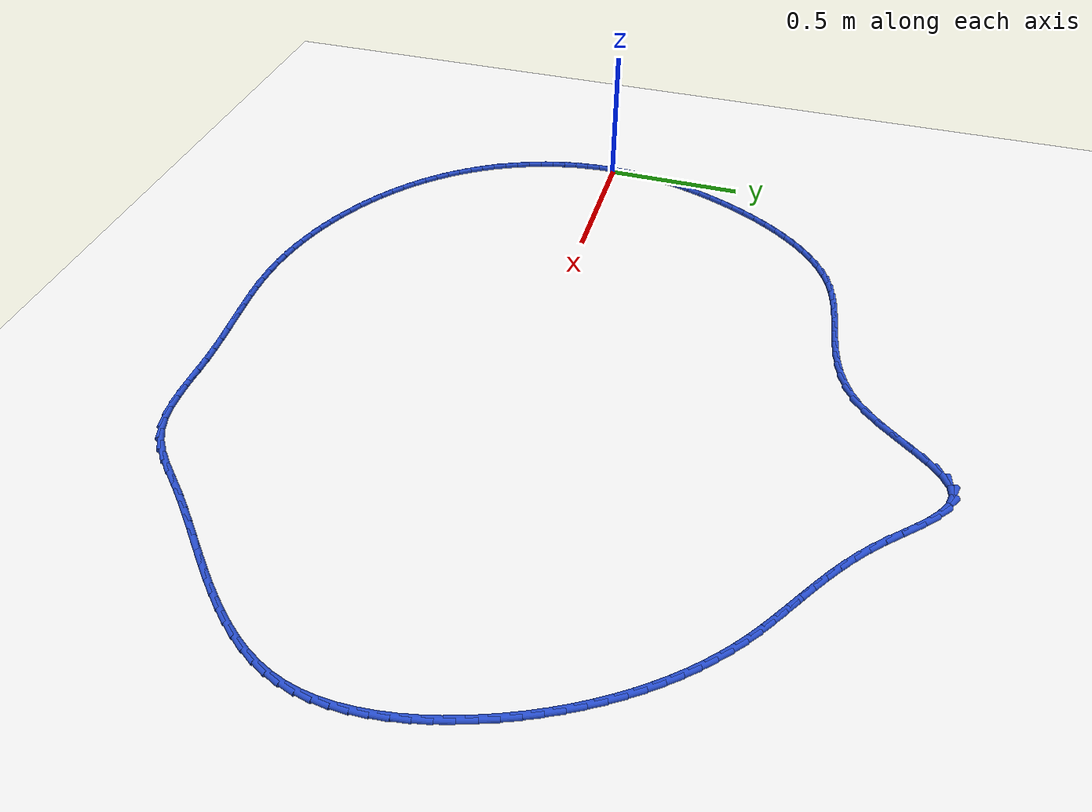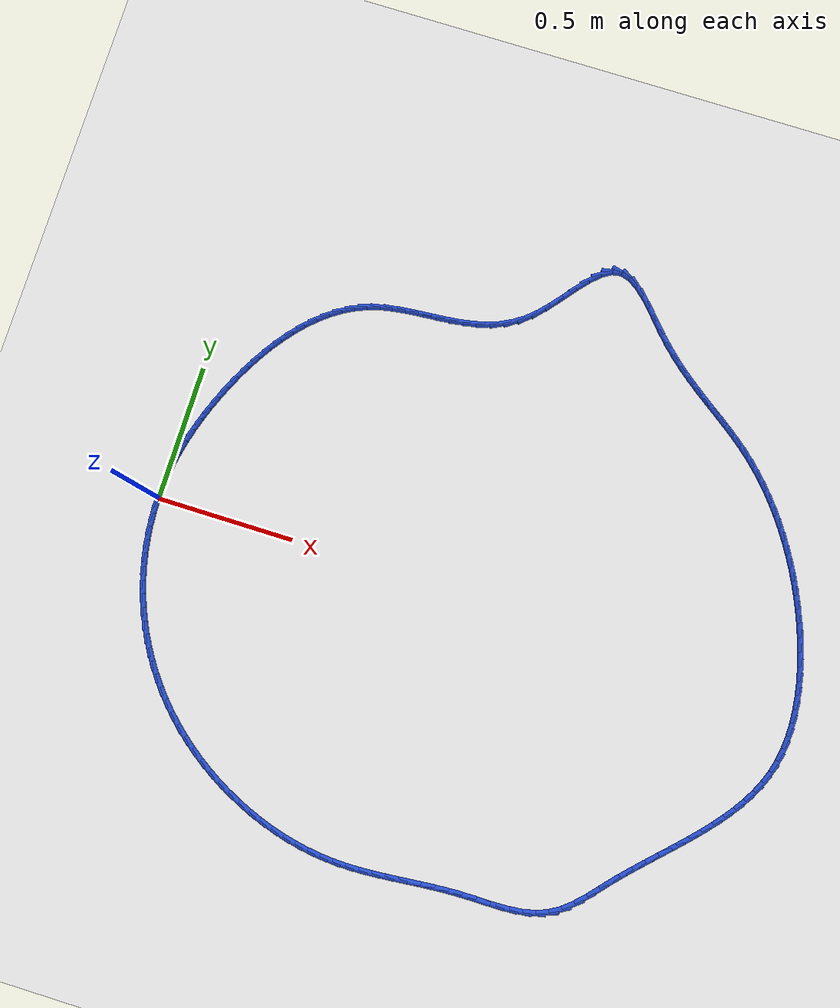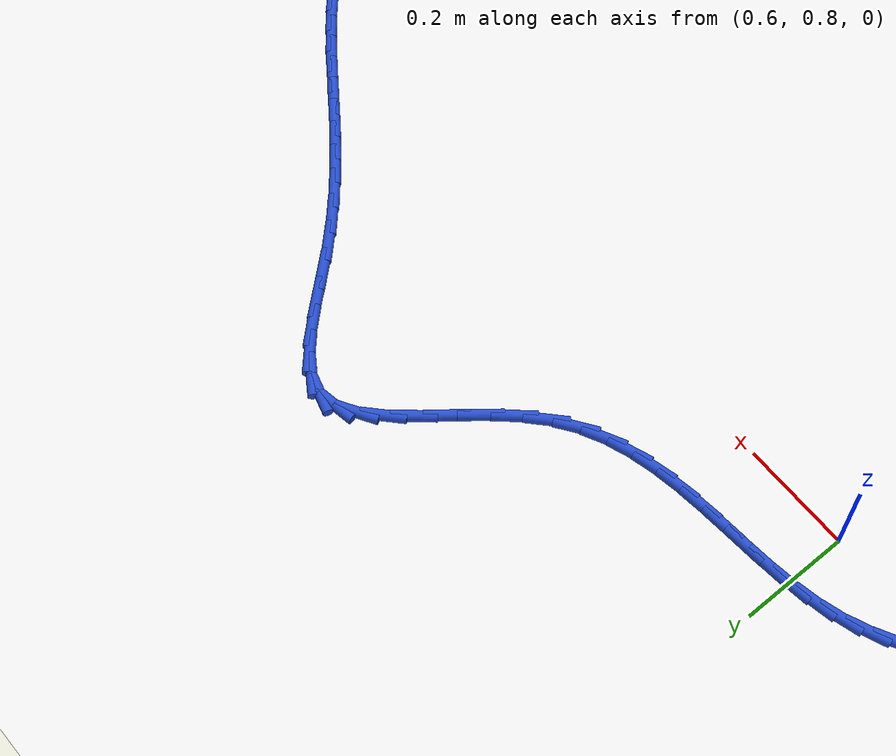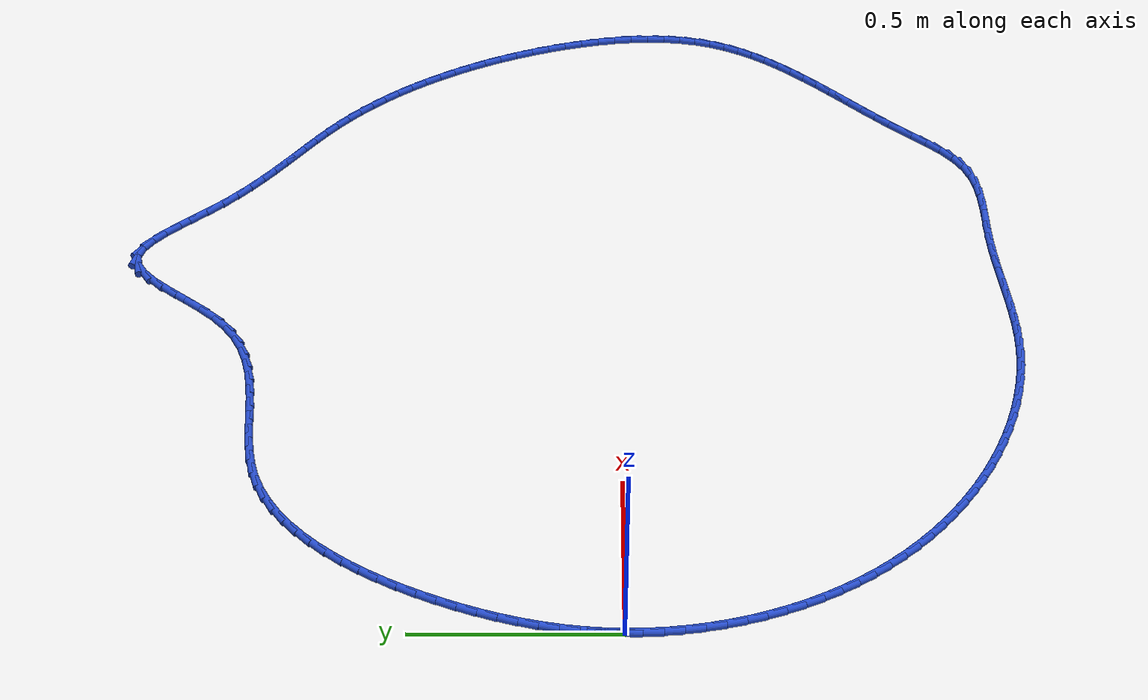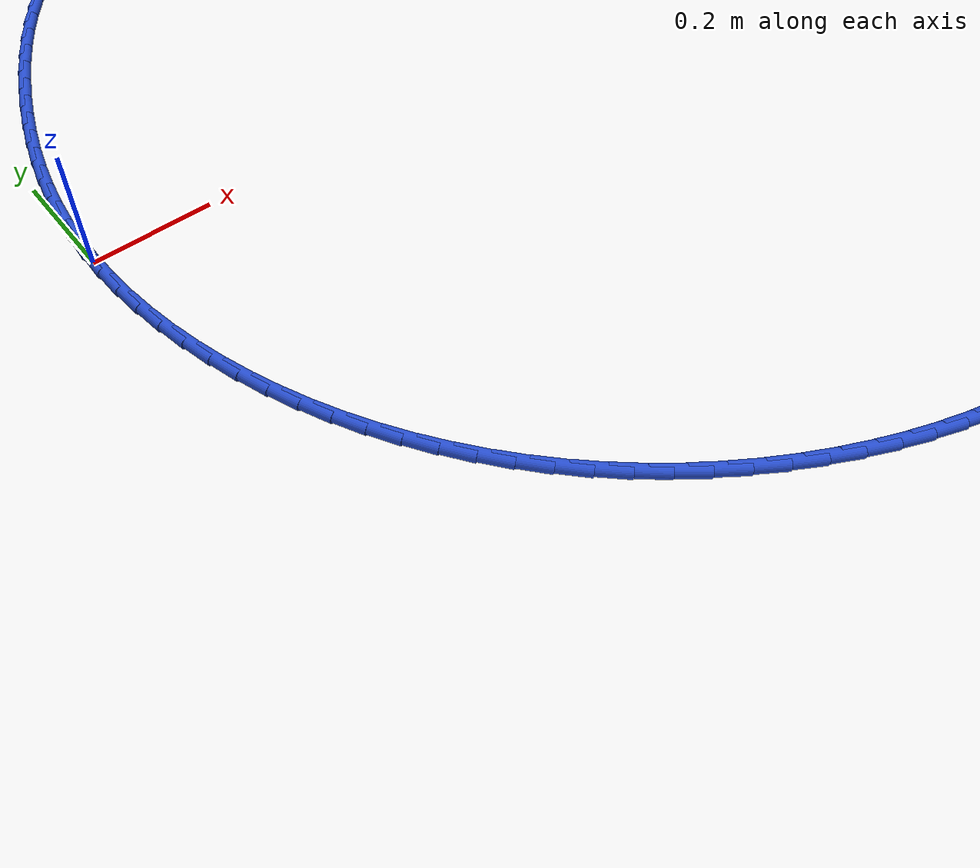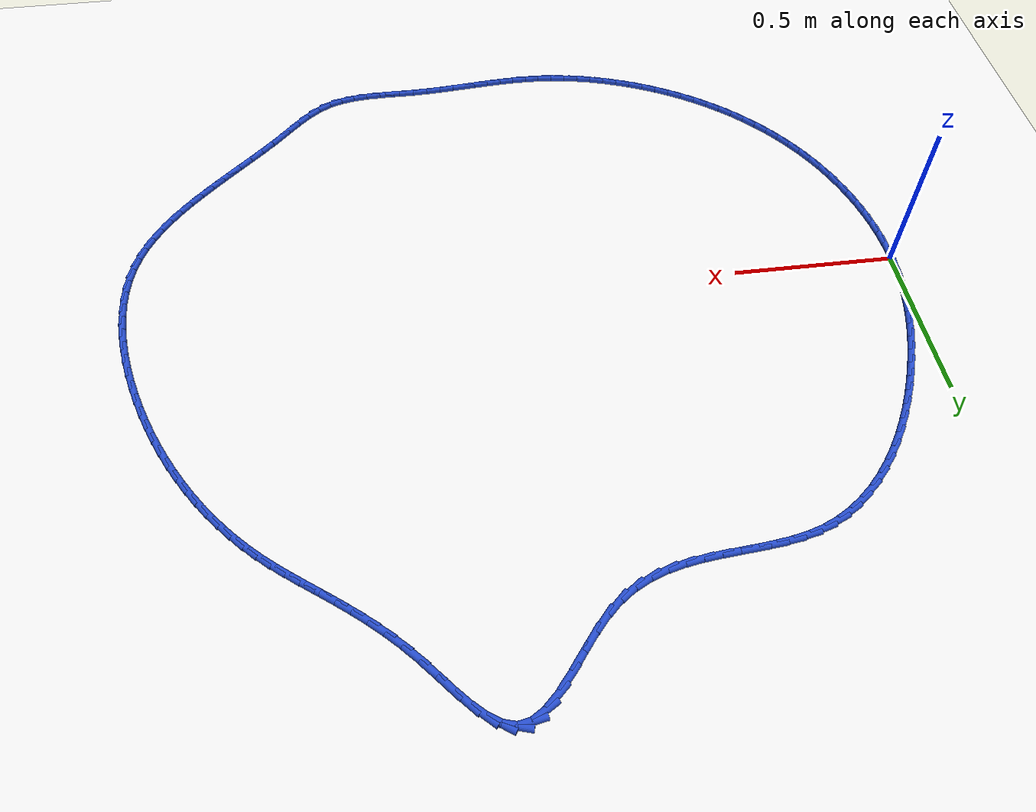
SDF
<sdf version="1.6">
 <world name="default">
  <light name="sun" type="directional">
   <pose>0 0 10 0 -0 0</pose>
   <diffuse>0.8 0.8 0.8 1</diffuse>
   <specular>0.2 0.2 0.2 1</specular>
   <attenuation>
    <range>1000</range>
    <constant>0.9</constant>
    <linear>0.01</linear>
    <quadratic>0.001</quadratic>
   </attenuation>
   <direction>-0.5 0.1 -0.9</direction>
  </light>
  <model name="ground_plane">
   <static>1</static>
   <link name="link">
    <collision name="collision">
     <geometry><plane><normal>0 0 1</normal><size>100 100</size></plane></geometry>
     <surface><friction><ode><mu>100</mu><mu2>50</mu2></ode></friction></surface>
    </collision>
    <visual name="visual">
     <cast_shadows>0</cast_shadows>
     <geometry><plane><normal>0 0 1</normal><size>100 100</size></plane></geometry>
     <material>
      <script><uri>file://media/materials/scripts/gazebo.material</uri><name>Gazebo/WhiteGlow</name></script>
     </material>
    </visual>
   </link>
  </model>
  <gravity>0 0 -9.8</gravity>
  <magnetic_field>6e-06 2.3e-05 -4.2e-05</magnetic_field>
  <atmosphere type="adiabatic"/>
  <physics name="default_physics" default="0" type="ode">
   <max_step_size>0.001</max_step_size>
   <real_time_factor>1</real_time_factor>
   <real_time_update_rate>1000</real_time_update_rate>
  </physics>
  <scene><ambient>0.4 0.4 0.4 1</ambient><background>0.7 0.7 0.7 1</background><shadows>1</shadows></scene>
  <spherical_coordinates>
   <surface_model>EARTH_WGS84</surface_model>
   <latitude_deg>0</latitude_deg>
   <longitude_deg>0</longitude_deg>
   <elevation>0</elevation>
   <heading_deg>0</heading_deg>
  </spherical_coordinates>
  <model name="line">
   <link name="link_0">
    <pose>-2.0816681711721685e-17 1.249000902703301e-16 0.01 0 1.57 1.5409839974002413</pose>
    <collision name="collision">
     <geometry><cylinder><radius>0.01</radius><length>0.08</length></cylinder></geometry>
    </collision>
    <visual name="visual">
     <material>
      <script><name>Gazebo/Blue</name><uri>file://media/materials/scripts/gazebo.material</uri></script>
     </material>
     <geometry><cylinder><radius>0.01</radius><length>0.08</length></cylinder></geometry>
    </visual>
   </link>
   <link name="link_1">
    <pose>0.001416774368375935 0.047509021973724294 0.01 0 1.57 1.4903407403062767</pose>
    <collision name="collision">
     <geometry><cylinder><radius>0.01</radius><length>0.08</length></cylinder></geometry>
    </collision>
    <visual name="visual">
     <material>
      <script><name>Gazebo/Blue</name><uri>file://media/materials/scripts/gazebo.material</uri></script>
     </material>
     <geometry><cylinder><radius>0.01</radius><length>0.08</length></cylinder></geometry>
    </visual>
   </link>
   <link name="link_2">
    <pose>0.0052270917090097594 0.0947660544927207 0.01 0 1.57 1.4412061075957883</pose>
    <collision name="collision">
     <geometry><cylinder><radius>0.01</radius><length>0.08</length></cylinder></geometry>
    </collision>
    <visual name="visual">
     <material>
      <script><name>Gazebo/Blue</name><uri>file://media/materials/scripts/gazebo.material</uri></script>
     </material>
     <geometry><cylinder><radius>0.01</radius><length>0.08</length></cylinder></geometry>
    </visual>
   </link>
   <link name="link_3">
    <pose>0.011358834308184814 0.141817285810648 0.01 0 1.57 1.3939315058798505</pose>
    <collision name="collision">
     <geometry><cylinder><radius>0.01</radius><length>0.08</length></cylinder></geometry>
    </collision>
    <visual name="visual">
     <material>
      <script><name>Gazebo/Blue</name><uri>file://media/materials/scripts/gazebo.material</uri></script>
     </material>
     <geometry><cylinder><radius>0.01</radius><length>0.08</length></cylinder></geometry>
    </visual>
   </link>
   <link name="link_4">
    <pose>0.01973988445218445 0.1887089041811647 0.01 0 1.57 1.34880754402212</pose>
    <collision name="collision">
     <geometry><cylinder><radius>0.01</radius><length>0.08</length></cylinder></geometry>
    </collision>
    <visual name="visual">
     <material>
      <script><name>Gazebo/Blue</name><uri>file://media/materials/scripts/gazebo.material</uri></script>
     </material>
     <geometry><cylinder><radius>0.01</radius><length>0.08</length></cylinder></geometry>
    </visual>
   </link>
   <link name="link_5">
    <pose>0.030298124427292017 0.2354870978579295 0.01 0 1.57 1.3060600844356591</pose>
    <collision name="collision">
     <geometry><cylinder><radius>0.01</radius><length>0.08</length></cylinder></geometry>
    </collision>
    <visual name="visual">
     <material>
      <script><name>Gazebo/Blue</name><uri>file://media/materials/scripts/gazebo.material</uri></script>
     </material>
     <geometry><cylinder><radius>0.01</radius><length>0.08</length></cylinder></geometry>
    </visual>
   </link>
   <link name="link_6">
    <pose>0.04296143651979088 0.282198055094601 0.01 0 1.57 1.2658509156572701</pose>
    <collision name="collision">
     <geometry><cylinder><radius>0.01</radius><length>0.08</length></cylinder></geometry>
    </collision>
    <visual name="visual">
     <material>
      <script><name>Gazebo/Blue</name><uri>file://media/materials/scripts/gazebo.material</uri></script>
     </material>
     <geometry><cylinder><radius>0.01</radius><length>0.08</length></cylinder></geometry>
    </visual>
   </link>
   <link name="link_7">
    <pose>0.0576577030159644 0.32888796414483773 0.01 0 1.57 1.2282820878308067</pose>
    <collision name="collision">
     <geometry><cylinder><radius>0.01</radius><length>0.08</length></cylinder></geometry>
    </collision>
    <visual name="visual">
     <material>
      <script><name>Gazebo/Blue</name><uri>file://media/materials/scripts/gazebo.material</uri></script>
     </material>
     <geometry><cylinder><radius>0.01</radius><length>0.08</length></cylinder></geometry>
    </visual>
   </link>
   <link name="link_8">
    <pose>0.07431480620209596 0.37560301326229845 0.01 0 1.57 1.19337467369707</pose>
    <collision name="collision">
     <geometry><cylinder><radius>0.01</radius><length>0.08</length></cylinder></geometry>
    </collision>
    <visual name="visual">
     <material>
      <script><name>Gazebo/Blue</name><uri>file://media/materials/scripts/gazebo.material</uri></script>
     </material>
     <geometry><cylinder><radius>0.01</radius><length>0.08</length></cylinder></geometry>
    </visual>
   </link>
   <link name="link_9">
    <pose>0.09286111316814986 0.4223867797617684 0.01 0 1.57 1.159395876455431</pose>
    <collision name="collision">
     <geometry><cylinder><radius>0.01</radius><length>0.08</length></cylinder></geometry>
    </collision>
    <visual name="visual">
     <material>
      <script><name>Gazebo/Blue</name><uri>file://media/materials/scripts/gazebo.material</uri></script>
     </material>
     <geometry><cylinder><radius>0.01</radius><length>0.08</length></cylinder></geometry>
    </visual>
   </link>
   <link name="link_10">
    <pose>0.11325387216319613 0.4691272997689585 0.01 0 1.57 1.123353978053719</pose>
    <collision name="collision">
     <geometry><cylinder><radius>0.01</radius><length>0.08</length></cylinder></geometry>
    </collision>
    <visual name="visual">
     <material>
      <script><name>Gazebo/Blue</name><uri>file://media/materials/scripts/gazebo.material</uri></script>
     </material>
     <geometry><cylinder><radius>0.01</radius><length>0.08</length></cylinder></geometry>
    </visual>
   </link>
   <link name="link_11">
    <pose>0.13549497857660014 0.5154721595971309 0.01 0 1.57 1.0844694708845348</pose>
    <collision name="collision">
     <geometry><cylinder><radius>0.01</radius><length>0.08</length></cylinder></geometry>
    </collision>
    <visual name="visual">
     <material>
      <script><name>Gazebo/Blue</name><uri>file://media/materials/scripts/gazebo.material</uri></script>
     </material>
     <geometry><cylinder><radius>0.01</radius><length>0.08</length></cylinder></geometry>
    </visual>
   </link>
   <link name="link_12">
    <pose>0.1595901545771456 0.5610483362128476 0.01 0 1.57 1.0421367316816996</pose>
    <collision name="collision">
     <geometry><cylinder><radius>0.01</radius><length>0.08</length></cylinder></geometry>
    </collision>
    <visual name="visual">
     <material>
      <script><name>Gazebo/Blue</name><uri>file://media/materials/scripts/gazebo.material</uri></script>
     </material>
     <geometry><cylinder><radius>0.01</radius><length>0.08</length></cylinder></geometry>
    </visual>
   </link>
   <link name="link_13">
    <pose>0.18554512233361642 0.6054828065826703 0.01 0 1.57 0.9956890752787328</pose>
    <collision name="collision">
     <geometry><cylinder><radius>0.01</radius><length>0.08</length></cylinder></geometry>
    </collision>
    <visual name="visual">
     <material>
      <script><name>Gazebo/Blue</name><uri>file://media/materials/scripts/gazebo.material</uri></script>
     </material>
     <geometry><cylinder><radius>0.01</radius><length>0.08</length></cylinder></geometry>
    </visual>
   </link>
   <link name="link_14">
    <pose>0.21336560401479646 0.6484025476731614 0.01 0 1.57 0.9443908749641493</pose>
    <collision name="collision">
     <geometry><cylinder><radius>0.01</radius><length>0.08</length></cylinder></geometry>
    </collision>
    <visual name="visual">
     <material>
      <script><name>Gazebo/Blue</name><uri>file://media/materials/scripts/gazebo.material</uri></script>
     </material>
     <geometry><cylinder><radius>0.01</radius><length>0.08</length></cylinder></geometry>
    </visual>
   </link>
   <link name="link_15">
    <pose>0.24305732178946954 0.6894345364508829 0.01 0 1.57 0.8874387240220154</pose>
    <collision name="collision">
     <geometry><cylinder><radius>0.01</radius><length>0.08</length></cylinder></geometry>
    </collision>
    <visual name="visual">
     <material>
      <script><name>Gazebo/Blue</name><uri>file://media/materials/scripts/gazebo.material</uri></script>
     </material>
     <geometry><cylinder><radius>0.01</radius><length>0.08</length></cylinder></geometry>
    </visual>
   </link>
   <link name="link_16">
    <pose>0.27462599782641944 0.7282057498823967 0.01 0 1.57 0.8239780340291915</pose>
    <collision name="collision">
     <geometry><cylinder><radius>0.01</radius><length>0.08</length></cylinder></geometry>
    </collision>
    <visual name="visual">
     <material>
      <script><name>Gazebo/Blue</name><uri>file://media/materials/scripts/gazebo.material</uri></script>
     </material>
     <geometry><cylinder><radius>0.01</radius><length>0.08</length></cylinder></geometry>
    </visual>
   </link>
   <link name="link_17">
    <pose>0.30807735429443006 0.7643431649342649 0.01 0 1.57 0.7531447976890759</pose>
    <collision name="collision">
     <geometry><cylinder><radius>0.01</radius><length>0.08</length></cylinder></geometry>
    </collision>
    <visual name="visual">
     <material>
      <script><name>Gazebo/Blue</name><uri>file://media/materials/scripts/gazebo.material</uri></script>
     </material>
     <geometry><cylinder><radius>0.01</radius><length>0.08</length></cylinder></geometry>
    </visual>
   </link>
   <link name="link_18">
    <pose>0.3434171133622853 0.79747375857305 0.01 0 1.57 0.6741452482695379</pose>
    <collision name="collision">
     <geometry><cylinder><radius>0.01</radius><length>0.08</length></cylinder></geometry>
    </collision>
    <visual name="visual">
     <material>
      <script><name>Gazebo/Blue</name><uri>file://media/materials/scripts/gazebo.material</uri></script>
     </material>
     <geometry><cylinder><radius>0.01</radius><length>0.08</length></cylinder></geometry>
    </visual>
   </link>
   <link name="link_19">
    <pose>0.3806509971987691 0.8272245077653136 0.01 0 1.57 0.5863861862324145</pose>
    <collision name="collision">
     <geometry><cylinder><radius>0.01</radius><length>0.08</length></cylinder></geometry>
    </collision>
    <visual name="visual">
     <material>
      <script><name>Gazebo/Blue</name><uri>file://media/materials/scripts/gazebo.material</uri></script>
     </material>
     <geometry><cylinder><radius>0.01</radius><length>0.08</length></cylinder></geometry>
    </visual>
   </link>
   <link name="link_20">
    <pose>0.41978472797266486 0.8532223894776179 0.01 0 1.57 0.48966066383717854</pose>
    <collision name="collision">
     <geometry><cylinder><radius>0.01</radius><length>0.08</length></cylinder></geometry>
    </collision>
    <visual name="visual">
     <material>
      <script><name>Gazebo/Blue</name><uri>file://media/materials/scripts/gazebo.material</uri></script>
     </material>
     <geometry><cylinder><radius>0.01</radius><length>0.08</length></cylinder></geometry>
    </visual>
   </link>
   <link name="link_21">
    <pose>0.460824027852757 0.875094380676525 0.01 0 1.57 0.3843709245489825</pose>
    <collision name="collision">
     <geometry><cylinder><radius>0.01</radius><length>0.08</length></cylinder></geometry>
    </collision>
    <visual name="visual">
     <material>
      <script><name>Gazebo/Blue</name><uri>file://media/materials/scripts/gazebo.material</uri></script>
     </material>
     <geometry><cylinder><radius>0.01</radius><length>0.08</length></cylinder></geometry>
    </visual>
   </link>
   <link name="link_22">
    <pose>0.503774619007829 0.8924674583285971 0.01 0 1.57 0.27609932247218366</pose>
    <collision name="collision">
     <geometry><cylinder><radius>0.01</radius><length>0.08</length></cylinder></geometry>
    </collision>
    <visual name="visual">
     <material>
      <script><name>Gazebo/Blue</name><uri>file://media/materials/scripts/gazebo.material</uri></script>
     </material>
     <geometry><cylinder><radius>0.01</radius><length>0.08</length></cylinder></geometry>
    </visual>
   </link>
   <link name="link_23">
    <pose>0.5485912730996741 0.9051656218235199 0.01 0 1.57 0.18766792251551653</pose>
    <collision name="collision">
     <geometry><cylinder><radius>0.01</radius><length>0.08</length></cylinder></geometry>
    </collision>
    <visual name="visual">
     <material>
      <script><name>Gazebo/Blue</name><uri>file://media/materials/scripts/gazebo.material</uri></script>
     </material>
     <geometry><cylinder><radius>0.01</radius><length>0.08</length></cylinder></geometry>
    </visual>
   </link>
   <link name="link_24">
    <pose>0.5949799644858897 0.913974954161815 0.01 0 1.57 0.12540876024514963</pose>
    <collision name="collision">
     <geometry><cylinder><radius>0.01</radius><length>0.08</length></cylinder></geometry>
    </collision>
    <visual name="visual">
     <material>
      <script><name>Gazebo/Blue</name><uri>file://media/materials/scripts/gazebo.material</uri></script>
     </material>
     <geometry><cylinder><radius>0.01</radius><length>0.08</length></cylinder></geometry>
    </visual>
   </link>
   <link name="link_25">
    <pose>0.642570841273715 0.9199747537105335 0.01 0 1.57 0.08794592201370506</pose>
    <collision name="collision">
     <geometry><cylinder><radius>0.01</radius><length>0.08</length></cylinder></geometry>
    </collision>
    <visual name="visual">
     <material>
      <script><name>Gazebo/Blue</name><uri>file://media/materials/scripts/gazebo.material</uri></script>
     </material>
     <geometry><cylinder><radius>0.01</radius><length>0.08</length></cylinder></geometry>
    </visual>
   </link>
   <link name="link_26">
    <pose>0.6909940333038781 0.9242443894721751 0.01 0 1.57 0.07389189313688703</pose>
    <collision name="collision">
     <geometry><cylinder><radius>0.01</radius><length>0.08</length></cylinder></geometry>
    </collision>
    <visual name="visual">
     <material>
      <script><name>Gazebo/Blue</name><uri>file://media/materials/scripts/gazebo.material</uri></script>
     </material>
     <geometry><cylinder><radius>0.01</radius><length>0.08</length></cylinder></geometry>
    </visual>
   </link>
   <link name="link_27">
    <pose>0.7398796704171086 0.9278632304492406 0.01 0 1.57 0.08244971559735163</pose>
    <collision name="collision">
     <geometry><cylinder><radius>0.01</radius><length>0.08</length></cylinder></geometry>
    </collision>
    <visual name="visual">
     <material>
      <script><name>Gazebo/Blue</name><uri>file://media/materials/scripts/gazebo.material</uri></script>
     </material>
     <geometry><cylinder><radius>0.01</radius><length>0.08</length></cylinder></geometry>
    </visual>
   </link>
   <link name="link_28">
    <pose>0.7888578824541354 0.9319106456442295 0.01 0 1.57 0.11357997765792925</pose>
    <collision name="collision">
     <geometry><cylinder><radius>0.01</radius><length>0.08</length></cylinder></geometry>
    </collision>
    <visual name="visual">
     <material>
      <script><name>Gazebo/Blue</name><uri>file://media/materials/scripts/gazebo.material</uri></script>
     </material>
     <geometry><cylinder><radius>0.01</radius><length>0.08</length></cylinder></geometry>
    </visual>
   </link>
   <link name="link_29">
    <pose>0.8375587992556878 0.9374660040596423 0.01 0 1.57 0.16785479780062</pose>
    <collision name="collision">
     <geometry><cylinder><radius>0.01</radius><length>0.08</length></cylinder></geometry>
    </collision>
    <visual name="visual">
     <material>
      <script><name>Gazebo/Blue</name><uri>file://media/materials/scripts/gazebo.material</uri></script>
     </material>
     <geometry><cylinder><radius>0.01</radius><length>0.08</length></cylinder></geometry>
    </visual>
   </link>
   <link name="link_30">
    <pose>0.8856125506624949 0.9456086746979793 0.01 0 1.57 0.24598234052987153</pose>
    <collision name="collision">
     <geometry><cylinder><radius>0.01</radius><length>0.08</length></cylinder></geometry>
    </collision>
    <visual name="visual">
     <material>
      <script><name>Gazebo/Blue</name><uri>file://media/materials/scripts/gazebo.material</uri></script>
     </material>
     <geometry><cylinder><radius>0.01</radius><length>0.08</length></cylinder></geometry>
    </visual>
   </link>
   <link name="link_31">
    <pose>0.9326492665152855 0.95741802656174 0.01 0 1.57 0.34790920960821775</pose>
    <collision name="collision">
     <geometry><cylinder><radius>0.01</radius><length>0.08</length></cylinder></geometry>
    </collision>
    <visual name="visual">
     <material>
      <script><name>Gazebo/Blue</name><uri>file://media/materials/scripts/gazebo.material</uri></script>
     </material>
     <geometry><cylinder><radius>0.01</radius><length>0.08</length></cylinder></geometry>
    </visual>
   </link>
   <link name="link_32">
    <pose>0.9782990766547889 0.9739734286534252 0.01 0 1.57 0.47153192324504506</pose>
    <collision name="collision">
     <geometry><cylinder><radius>0.01</radius><length>0.08</length></cylinder></geometry>
    </collision>
    <visual name="visual">
     <material>
      <script><name>Gazebo/Blue</name><uri>file://media/materials/scripts/gazebo.material</uri></script>
     </material>
     <geometry><cylinder><radius>0.01</radius><length>0.08</length></cylinder></geometry>
    </visual>
   </link>
   <link name="link_33">
    <pose>1.022192110921734 0.9963542499755345 0.01 0 1.57 0.6115151194935744</pose>
    <collision name="collision">
     <geometry><cylinder><radius>0.01</radius><length>0.08</length></cylinder></geometry>
    </collision>
    <visual name="visual">
     <material>
      <script><name>Gazebo/Blue</name><uri>file://media/materials/scripts/gazebo.material</uri></script>
     </material>
     <geometry><cylinder><radius>0.01</radius><length>0.08</length></cylinder></geometry>
    </visual>
   </link>
   <link name="link_34">
    <pose>1.0639584991568505 1.0256398595305685 0.01 0 1.57 0.7512235024314385</pose>
    <collision name="collision">
     <geometry><cylinder><radius>0.01</radius><length>0.08</length></cylinder></geometry>
    </collision>
    <visual name="visual">
     <material>
      <script><name>Gazebo/Blue</name><uri>file://media/materials/scripts/gazebo.material</uri></script>
     </material>
     <geometry><cylinder><radius>0.01</radius><length>0.08</length></cylinder></geometry>
    </visual>
   </link>
   <link name="link_35">
    <pose>1.103324843766285 1.0624034752293818 0.01 0 1.57 0.8455147471034684</pose>
    <collision name="collision">
     <geometry><cylinder><radius>0.01</radius><length>0.08</length></cylinder></geometry>
    </collision>
    <visual name="visual">
     <material>
      <script><name>Gazebo/Blue</name><uri>file://media/materials/scripts/gazebo.material</uri></script>
     </material>
     <geometry><cylinder><radius>0.01</radius><length>0.08</length></cylinder></geometry>
    </visual>
   </link>
   <link name="link_36">
    <pose>1.1405545635812055 1.1044018643332651 0.01 0 1.57 0.8915097424041345</pose>
    <collision name="collision">
     <geometry><cylinder><radius>0.01</radius><length>0.08</length></cylinder></geometry>
    </collision>
    <visual name="visual">
     <material>
      <script><name>Gazebo/Blue</name><uri>file://media/materials/scripts/gazebo.material</uri></script>
     </material>
     <geometry><cylinder><radius>0.01</radius><length>0.08</length></cylinder></geometry>
    </visual>
   </link>
   <link name="link_37">
    <pose>1.1760967063857157 1.1484178768373656 0.01 0 1.57 0.895324501023182</pose>
    <collision name="collision">
     <geometry><cylinder><radius>0.01</radius><length>0.08</length></cylinder></geometry>
    </collision>
    <visual name="visual">
     <material>
      <script><name>Gazebo/Blue</name><uri>file://media/materials/scripts/gazebo.material</uri></script>
     </material>
     <geometry><cylinder><radius>0.01</radius><length>0.08</length></cylinder></geometry>
    </visual>
   </link>
   <link name="link_38">
    <pose>1.2104004981334269 1.1912334279561492 0.01 0 1.57 0.8531876766705634</pose>
    <collision name="collision">
     <geometry><cylinder><radius>0.01</radius><length>0.08</length></cylinder></geometry>
    </collision>
    <visual name="visual">
     <material>
      <script><name>Gazebo/Blue</name><uri>file://media/materials/scripts/gazebo.material</uri></script>
     </material>
     <geometry><cylinder><radius>0.01</radius><length>0.08</length></cylinder></geometry>
    </visual>
   </link>
   <link name="link_39">
    <pose>1.2439151647779503 1.2296304329040832 0.01 0 1.57 0.7476529306380669</pose>
    <collision name="collision">
     <geometry><cylinder><radius>0.01</radius><length>0.08</length></cylinder></geometry>
    </collision>
    <visual name="visual">
     <material>
      <script><name>Gazebo/Blue</name><uri>file://media/materials/scripts/gazebo.material</uri></script>
     </material>
     <geometry><cylinder><radius>0.01</radius><length>0.08</length></cylinder></geometry>
    </visual>
   </link>
   <link name="link_40">
    <pose>1.277089932272896 1.2603908068956342 0.01 0 1.57 0.5389867812209073</pose>
    <collision name="collision">
     <geometry><cylinder><radius>0.01</radius><length>0.08</length></cylinder></geometry>
    </collision>
    <visual name="visual">
     <material>
      <script><name>Gazebo/Blue</name><uri>file://media/materials/scripts/gazebo.material</uri></script>
     </material>
     <geometry><cylinder><radius>0.01</radius><length>0.08</length></cylinder></geometry>
    </visual>
   </link>
   <link name="link_41">
    <pose>1.3103740265718757 1.2802964651452695 0.01 0 1.57 0.17068788245969396</pose>
    <collision name="collision">
     <geometry><cylinder><radius>0.01</radius><length>0.08</length></cylinder></geometry>
    </collision>
    <visual name="visual">
     <material>
      <script><name>Gazebo/Blue</name><uri>file://media/materials/scripts/gazebo.material</uri></script>
     </material>
     <geometry><cylinder><radius>0.01</radius><length>0.08</length></cylinder></geometry>
    </visual>
   </link>
   <link name="link_42">
    <pose>1.344216637929233 1.2861297487998196 0.01 0 1.57 -0.28239064304076633</pose>
    <collision name="collision">
     <geometry><cylinder><radius>0.01</radius><length>0.08</length></cylinder></geometry>
    </collision>
    <visual name="visual">
     <material>
      <script><name>Gazebo/Blue</name><uri>file://media/materials/scripts/gazebo.material</uri></script>
     </material>
     <geometry><cylinder><radius>0.01</radius><length>0.08</length></cylinder></geometry>
    </visual>
   </link>
   <link name="link_43">
    <pose>1.3789514058458294 1.2760516493430267 0.01 0 1.57 -0.5813778236442951</pose>
    <collision name="collision">
     <geometry><cylinder><radius>0.01</radius><length>0.08</length></cylinder></geometry>
    </collision>
    <visual name="visual">
     <material>
      <script><name>Gazebo/Blue</name><uri>file://media/materials/scripts/gazebo.material</uri></script>
     </material>
     <geometry><cylinder><radius>0.01</radius><length>0.08</length></cylinder></geometry>
    </visual>
   </link>
   <link name="link_44">
    <pose>1.414539662680874 1.2526652008312225 0.01 0 1.57 -0.7404187485544215</pose>
    <collision name="collision">
     <geometry><cylinder><radius>0.01</radius><length>0.08</length></cylinder></geometry>
    </collision>
    <visual name="visual">
     <material>
      <script><name>Gazebo/Blue</name><uri>file://media/materials/scripts/gazebo.material</uri></script>
     </material>
     <geometry><cylinder><radius>0.01</radius><length>0.08</length></cylinder></geometry>
    </visual>
   </link>
   <link name="link_45">
    <pose>1.4508679009670506 1.219466360550932 0.01 0 1.57 -0.8188701993541283</pose>
    <collision name="collision">
     <geometry><cylinder><radius>0.01</radius><length>0.08</length></cylinder></geometry>
    </collision>
    <visual name="visual">
     <material>
      <script><name>Gazebo/Blue</name><uri>file://media/materials/scripts/gazebo.material</uri></script>
     </material>
     <geometry><cylinder><radius>0.01</radius><length>0.08</length></cylinder></geometry>
    </visual>
   </link>
   <link name="link_46">
    <pose>1.4878226132370451 1.1799510857886837 0.01 0 1.57 -0.8463234692321512</pose>
    <collision name="collision">
     <geometry><cylinder><radius>0.01</radius><length>0.08</length></cylinder></geometry>
    </collision>
    <visual name="visual">
     <material>
      <script><name>Gazebo/Blue</name><uri>file://media/materials/scripts/gazebo.material</uri></script>
     </material>
     <geometry><cylinder><radius>0.01</radius><length>0.08</length></cylinder></geometry>
    </visual>
   </link>
   <link name="link_47">
    <pose>1.525290292023541 1.1376153338310022 0.01 0 1.57 -0.8330621107804461</pose>
    <collision name="collision">
     <geometry><cylinder><radius>0.01</radius><length>0.08</length></cylinder></geometry>
    </collision>
    <visual name="visual">
     <material>
      <script><name>Gazebo/Blue</name><uri>file://media/materials/scripts/gazebo.material</uri></script>
     </material>
     <geometry><cylinder><radius>0.01</radius><length>0.08</length></cylinder></geometry>
    </visual>
   </link>
   <link name="link_48">
    <pose>1.5631574290490504 1.0959547169512265 0.01 0 1.57 -0.7878426848968224</pose>
    <collision name="collision">
     <geometry><cylinder><radius>0.01</radius><length>0.08</length></cylinder></geometry>
    </collision>
    <visual name="visual">
     <material>
      <script><name>Gazebo/Blue</name><uri>file://media/materials/scripts/gazebo.material</uri></script>
     </material>
     <geometry><cylinder><radius>0.01</radius><length>0.08</length></cylinder></geometry>
    </visual>
   </link>
   <link name="link_49">
    <pose>1.6013085242494203 1.0576166419574033 0.01 0 1.57 -0.7408209924492719</pose>
    <collision name="collision">
     <geometry><cylinder><radius>0.01</radius><length>0.08</length></cylinder></geometry>
    </collision>
    <visual name="visual">
     <material>
      <script><name>Gazebo/Blue</name><uri>file://media/materials/scripts/gazebo.material</uri></script>
     </material>
     <geometry><cylinder><radius>0.01</radius><length>0.08</length></cylinder></geometry>
    </visual>
   </link>
   <link name="link_50">
    <pose>1.6396218006115766 1.022575467149405 0.01 0 1.57 -0.6998679395506957</pose>
    <collision name="collision">
     <geometry><cylinder><radius>0.01</radius><length>0.08</length></cylinder></geometry>
    </collision>
    <visual name="visual">
     <material>
      <script><name>Gazebo/Blue</name><uri>file://media/materials/scripts/gazebo.material</uri></script>
     </material>
     <geometry><cylinder><radius>0.01</radius><length>0.08</length></cylinder></geometry>
    </visual>
   </link>
   <link name="link_51">
    <pose>1.6779742477182402 0.9902803037179161 0.01 0 1.57 -0.6664836108621648</pose>
    <collision name="collision">
     <geometry><cylinder><radius>0.01</radius><length>0.08</length></cylinder></geometry>
    </collision>
    <visual name="visual">
     <material>
      <script><name>Gazebo/Blue</name><uri>file://media/materials/scripts/gazebo.material</uri></script>
     </material>
     <geometry><cylinder><radius>0.01</radius><length>0.08</length></cylinder></geometry>
    </visual>
   </link>
   <link name="link_52">
    <pose>1.716242855152132 0.9601802628536195 0.01 0 1.57 -0.6419774500906644</pose>
    <collision name="collision">
     <geometry><cylinder><radius>0.01</radius><length>0.08</length></cylinder></geometry>
    </collision>
    <visual name="visual">
     <material>
      <script><name>Gazebo/Blue</name><uri>file://media/materials/scripts/gazebo.material</uri></script>
     </material>
     <geometry><cylinder><radius>0.01</radius><length>0.08</length></cylinder></geometry>
    </visual>
   </link>
   <link name="link_53">
    <pose>1.7543046124959716 0.9317244557471985 0.01 0 1.57 -0.6274269518577951</pose>
    <collision name="collision">
     <geometry><cylinder><radius>0.01</radius><length>0.08</length></cylinder></geometry>
    </collision>
    <visual name="visual">
     <material>
      <script><name>Gazebo/Blue</name><uri>file://media/materials/scripts/gazebo.material</uri></script>
     </material>
     <geometry><cylinder><radius>0.01</radius><length>0.08</length></cylinder></geometry>
    </visual>
   </link>
   <link name="link_54">
    <pose>1.7920365093324808 0.9043619935893369 0.01 0 1.57 -0.6236538561690059</pose>
    <collision name="collision">
     <geometry><cylinder><radius>0.01</radius><length>0.08</length></cylinder></geometry>
    </collision>
    <visual name="visual">
     <material>
      <script><name>Gazebo/Blue</name><uri>file://media/materials/scripts/gazebo.material</uri></script>
     </material>
     <geometry><cylinder><radius>0.01</radius><length>0.08</length></cylinder></geometry>
    </visual>
   </link>
   <link name="link_55">
    <pose>1.8293155352443795 0.8775419875707181 0.01 0 1.57 -0.6312021035667263</pose>
    <collision name="collision">
     <geometry><cylinder><radius>0.01</radius><length>0.08</length></cylinder></geometry>
    </collision>
    <visual name="visual">
     <material>
      <script><name>Gazebo/Blue</name><uri>file://media/materials/scripts/gazebo.material</uri></script>
     </material>
     <geometry><cylinder><radius>0.01</radius><length>0.08</length></cylinder></geometry>
    </visual>
   </link>
   <link name="link_56">
    <pose>1.866018679814388 0.8507135488820257 0.01 0 1.57 -0.6503021369050908</pose>
    <collision name="collision">
     <geometry><cylinder><radius>0.01</radius><length>0.08</length></cylinder></geometry>
    </collision>
    <visual name="visual">
     <material>
      <script><name>Gazebo/Blue</name><uri>file://media/materials/scripts/gazebo.material</uri></script>
     </material>
     <geometry><cylinder><radius>0.01</radius><length>0.08</length></cylinder></geometry>
    </visual>
   </link>
   <link name="link_57">
    <pose>1.9020229326252278 0.8233257887139428 0.01 0 1.57 -0.6808134018103794</pose>
    <collision name="collision">
     <geometry><cylinder><radius>0.01</radius><length>0.08</length></cylinder></geometry>
    </collision>
    <visual name="visual">
     <material>
      <script><name>Gazebo/Blue</name><uri>file://media/materials/scripts/gazebo.material</uri></script>
     </material>
     <geometry><cylinder><radius>0.01</radius><length>0.08</length></cylinder></geometry>
    </visual>
   </link>
   <link name="link_58">
    <pose>1.9372052832596194 0.7948278182571529 0.01 0 1.57 -0.7216338790706674</pose>
    <collision name="collision">
     <geometry><cylinder><radius>0.01</radius><length>0.08</length></cylinder></geometry>
    </collision>
    <visual name="visual">
     <material>
      <script><name>Gazebo/Blue</name><uri>file://media/materials/scripts/gazebo.material</uri></script>
     </material>
     <geometry><cylinder><radius>0.01</radius><length>0.08</length></cylinder></geometry>
    </visual>
   </link>
   <link name="link_59">
    <pose>1.971446335415138 0.7646969665268483 0.01 0 1.57 -0.7655408222909443</pose>
    <collision name="collision">
     <geometry><cylinder><radius>0.01</radius><length>0.08</length></cylinder></geometry>
    </collision>
    <visual name="visual">
     <material>
      <script><name>Gazebo/Blue</name><uri>file://media/materials/scripts/gazebo.material</uri></script>
     </material>
     <geometry><cylinder><radius>0.01</radius><length>0.08</length></cylinder></geometry>
    </visual>
   </link>
   <link name="link_60">
    <pose>2.004672115926962 0.7327652115122247 0.01 0 1.57 -0.8080452044715579</pose>
    <collision name="collision">
     <geometry><cylinder><radius>0.01</radius><length>0.08</length></cylinder></geometry>
    </collision>
    <visual name="visual">
     <material>
      <script><name>Gazebo/Blue</name><uri>file://media/materials/scripts/gazebo.material</uri></script>
     </material>
     <geometry><cylinder><radius>0.01</radius><length>0.08</length></cylinder></geometry>
    </visual>
   </link>
   <link name="link_61">
    <pose>2.03683966130102 0.6991066445503702 0.01 0 1.57 -0.8491873050449519</pose>
    <collision name="collision">
     <geometry><cylinder><radius>0.01</radius><length>0.08</length></cylinder></geometry>
    </collision>
    <visual name="visual">
     <material>
      <script><name>Gazebo/Blue</name><uri>file://media/materials/scripts/gazebo.material</uri></script>
     </material>
     <geometry><cylinder><radius>0.01</radius><length>0.08</length></cylinder></geometry>
    </visual>
   </link>
   <link name="link_62">
    <pose>2.0679066071387933 0.6638000345201284 0.01 0 1.57 -0.8890954699583018</pose>
    <collision name="collision">
     <geometry><cylinder><radius>0.01</radius><length>0.08</length></cylinder></geometry>
    </collision>
    <visual name="visual">
     <material>
      <script><name>Gazebo/Blue</name><uri>file://media/materials/scripts/gazebo.material</uri></script>
     </material>
     <geometry><cylinder><radius>0.01</radius><length>0.08</length></cylinder></geometry>
    </visual>
   </link>
   <link name="link_63">
    <pose>2.0978305890417643 0.6269241503003451 0.01 0 1.57 -0.9278983278952256</pose>
    <collision name="collision">
     <geometry><cylinder><radius>0.01</radius><length>0.08</length></cylinder></geometry>
    </collision>
    <visual name="visual">
     <material>
      <script><name>Gazebo/Blue</name><uri>file://media/materials/scripts/gazebo.material</uri></script>
     </material>
     <geometry><cylinder><radius>0.01</radius><length>0.08</length></cylinder></geometry>
    </visual>
   </link>
   <link name="link_64">
    <pose>2.1265692426114127 0.588557760769864 0.01 0 1.57 -0.9657232677484174</pose>
    <collision name="collision">
     <geometry><cylinder><radius>0.01</radius><length>0.08</length></cylinder></geometry>
    </collision>
    <visual name="visual">
     <material>
      <script><name>Gazebo/Blue</name><uri>file://media/materials/scripts/gazebo.material</uri></script>
     </material>
     <geometry><cylinder><radius>0.01</radius><length>0.08</length></cylinder></geometry>
    </visual>
   </link>
   <link name="link_65">
    <pose>2.15408020344922 0.5487796348075299 0.01 0 1.57 -1.0026953933297609</pose>
    <collision name="collision">
     <geometry><cylinder><radius>0.01</radius><length>0.08</length></cylinder></geometry>
    </collision>
    <visual name="visual">
     <material>
      <script><name>Gazebo/Blue</name><uri>file://media/materials/scripts/gazebo.material</uri></script>
     </material>
     <geometry><cylinder><radius>0.01</radius><length>0.08</length></cylinder></geometry>
    </visual>
   </link>
   <link name="link_66">
    <pose>2.18032110715667 0.5076685412921871 0.01 0 1.57 -1.0389368538162216</pose>
    <collision name="collision">
     <geometry><cylinder><radius>0.01</radius><length>0.08</length></cylinder></geometry>
    </collision>
    <visual name="visual">
     <material>
      <script><name>Gazebo/Blue</name><uri>file://media/materials/scripts/gazebo.material</uri></script>
     </material>
     <geometry><cylinder><radius>0.01</radius><length>0.08</length></cylinder></geometry>
    </visual>
   </link>
   <link name="link_67">
    <pose>2.20524958933524 0.4653032491026798 0.01 0 1.57 -1.074566461466935</pose>
    <collision name="collision">
     <geometry><cylinder><radius>0.01</radius><length>0.08</length></cylinder></geometry>
    </collision>
    <visual name="visual">
     <material>
      <script><name>Gazebo/Blue</name><uri>file://media/materials/scripts/gazebo.material</uri></script>
     </material>
     <geometry><cylinder><radius>0.01</radius><length>0.08</length></cylinder></geometry>
    </visual>
   </link>
   <link name="link_68">
    <pose>2.2288232855864147 0.42176252711785317 0.01 0 1.57 -1.1096995216364793</pose>
    <collision name="collision">
     <geometry><cylinder><radius>0.01</radius><length>0.08</length></cylinder></geometry>
    </collision>
    <visual name="visual">
     <material>
      <script><name>Gazebo/Blue</name><uri>file://media/materials/scripts/gazebo.material</uri></script>
     </material>
     <geometry><cylinder><radius>0.01</radius><length>0.08</length></cylinder></geometry>
    </visual>
   </link>
   <link name="link_69">
    <pose>2.2509998315116735 0.3771251442165513 0.01 0 1.57 -1.144447812680657</pose>
    <collision name="collision">
     <geometry><cylinder><radius>0.01</radius><length>0.08</length></cylinder></geometry>
    </collision>
    <visual name="visual">
     <material>
      <script><name>Gazebo/Blue</name><uri>file://media/materials/scripts/gazebo.material</uri></script>
     </material>
     <geometry><cylinder><radius>0.01</radius><length>0.08</length></cylinder></geometry>
    </visual>
   </link>
   <link name="link_70">
    <pose>2.2717368627124976 0.3314698692776187 0.01 0 1.57 -1.1789196643173074</pose>
    <collision name="collision">
     <geometry><cylinder><radius>0.01</radius><length>0.08</length></cylinder></geometry>
    </collision>
    <visual name="visual">
     <material>
      <script><name>Gazebo/Blue</name><uri>file://media/materials/scripts/gazebo.material</uri></script>
     </material>
     <geometry><cylinder><radius>0.01</radius><length>0.08</length></cylinder></geometry>
    </visual>
   </link>
   <link name="link_71">
    <pose>2.29099201479037 0.2848754711798995 0.01 0 1.57 -1.2132200920912526</pose>
    <collision name="collision">
     <geometry><cylinder><radius>0.01</radius><length>0.08</length></cylinder></geometry>
    </collision>
    <visual name="visual">
     <material>
      <script><name>Gazebo/Blue</name><uri>file://media/materials/scripts/gazebo.material</uri></script>
     </material>
     <geometry><cylinder><radius>0.01</radius><length>0.08</length></cylinder></geometry>
    </visual>
   </link>
   <link name="link_72">
    <pose>2.3087229233467705 0.23742071880223897 0.01 0 1.57 -1.2476134934394438</pose>
    <collision name="collision">
     <geometry><cylinder><radius>0.01</radius><length>0.08</length></cylinder></geometry>
    </collision>
    <visual name="visual">
     <material>
      <script><name>Gazebo/Blue</name><uri>file://media/materials/scripts/gazebo.material</uri></script>
     </material>
     <geometry><cylinder><radius>0.01</radius><length>0.08</length></cylinder></geometry>
    </visual>
   </link>
   <link name="link_73">
    <pose>2.3248755414399787 0.1891932254072393 0.01 0 1.57 -1.28401083724129</pose>
    <collision name="collision">
     <geometry><cylinder><radius>0.01</radius><length>0.08</length></cylinder></geometry>
    </collision>
    <visual name="visual">
     <material>
      <script><name>Gazebo/Blue</name><uri>file://media/materials/scripts/gazebo.material</uri></script>
     </material>
     <geometry><cylinder><radius>0.01</radius><length>0.08</length></cylinder></geometry>
    </visual>
   </link>
   <link name="link_74">
    <pose>2.3392732609629903 0.1403733903881421 0.01 0 1.57 -1.323925362202529</pose>
    <collision name="collision">
     <geometry><cylinder><radius>0.01</radius><length>0.08</length></cylinder></geometry>
    </collision>
    <visual name="visual">
     <material>
      <script><name>Gazebo/Blue</name><uri>file://media/materials/scripts/gazebo.material</uri></script>
     </material>
     <geometry><cylinder><radius>0.01</radius><length>0.08</length></cylinder></geometry>
    </visual>
   </link>
   <link name="link_75">
    <pose>2.3516662697518123 0.09119703298654555 0.01 0 1.57 -1.3679795398499448</pose>
    <collision name="collision">
     <geometry><cylinder><radius>0.01</radius><length>0.08</length></cylinder></geometry>
    </collision>
    <visual name="visual">
     <material>
      <script><name>Gazebo/Blue</name><uri>file://media/materials/scripts/gazebo.material</uri></script>
     </material>
     <geometry><cylinder><radius>0.01</radius><length>0.08</length></cylinder></geometry>
    </visual>
   </link>
   <link name="link_76">
    <pose>2.361803774032875 0.041900715581194285 0.01 0 1.57 -1.416854225507179</pose>
    <collision name="collision">
     <geometry><cylinder><radius>0.01</radius><length>0.08</length></cylinder></geometry>
    </collision>
    <visual name="visual">
     <material>
      <script><name>Gazebo/Blue</name><uri>file://media/materials/scripts/gazebo.material</uri></script>
     </material>
     <geometry><cylinder><radius>0.01</radius><length>0.08</length></cylinder></geometry>
    </visual>
   </link>
   <link name="link_77">
    <pose>2.369434980032606 -0.007278999449166249 0.01 0 1.57 -1.4713008723688794</pose>
    <collision name="collision">
     <geometry><cylinder><radius>0.01</radius><length>0.08</length></cylinder></geometry>
    </collision>
    <visual name="visual">
     <material>
      <script><name>Gazebo/Blue</name><uri>file://media/materials/scripts/gazebo.material</uri></script>
     </material>
     <geometry><cylinder><radius>0.01</radius><length>0.08</length></cylinder></geometry>
    </visual>
   </link>
   <link name="link_78">
    <pose>2.374309093977437 -0.056105549725790405 0.01 0 1.57 -1.5321267443274236</pose>
    <collision name="collision">
     <geometry><cylinder><radius>0.01</radius><length>0.08</length></cylinder></geometry>
    </collision>
    <visual name="visual">
     <material>
      <script><name>Gazebo/Blue</name><uri>file://media/materials/scripts/gazebo.material</uri></script>
     </material>
     <geometry><cylinder><radius>0.01</radius><length>0.08</length></cylinder></geometry>
    </visual>
   </link>
   <link name="link_79">
    <pose>2.376175322093798 -0.10434237286993477 0.01 0 1.57 1.541434680574913</pose>
    <collision name="collision">
     <geometry><cylinder><radius>0.01</radius><length>0.08</length></cylinder></geometry>
    </collision>
    <visual name="visual">
     <material>
      <script><name>Gazebo/Blue</name><uri>file://media/materials/scripts/gazebo.material</uri></script>
     </material>
     <geometry><cylinder><radius>0.01</radius><length>0.08</length></cylinder></geometry>
    </visual>
   </link>
   <link name="link_80">
    <pose>2.374782870608116 -0.15175290650285275 0.01 0 1.57 1.4654238759519553</pose>
    <collision name="collision">
     <geometry><cylinder><radius>0.01</radius><length>0.08</length></cylinder></geometry>
    </collision>
    <visual name="visual">
     <material>
      <script><name>Gazebo/Blue</name><uri>file://media/materials/scripts/gazebo.material</uri></script>
     </material>
     <geometry><cylinder><radius>0.01</radius><length>0.08</length></cylinder></geometry>
    </visual>
   </link>
   <link name="link_81">
    <pose>2.369880945746822 -0.19810058824580096 0.01 0 1.57 1.3808280831557527</pose>
    <collision name="collision">
     <geometry><cylinder><radius>0.01</radius><length>0.08</length></cylinder></geometry>
    </collision>
    <visual name="visual">
     <material>
      <script><name>Gazebo/Blue</name><uri>file://media/materials/scripts/gazebo.material</uri></script>
     </material>
     <geometry><cylinder><radius>0.01</radius><length>0.08</length></cylinder></geometry>
    </visual>
   </link>
   <link name="link_82">
    <pose>2.3612187537363445 -0.2431488557200337 0.01 0 1.57 1.2875746226936042</pose>
    <collision name="collision">
     <geometry><cylinder><radius>0.01</radius><length>0.08</length></cylinder></geometry>
    </collision>
    <visual name="visual">
     <material>
      <script><name>Gazebo/Blue</name><uri>file://media/materials/scripts/gazebo.material</uri></script>
     </material>
     <geometry><cylinder><radius>0.01</radius><length>0.08</length></cylinder></geometry>
    </visual>
   </link>
   <link name="link_83">
    <pose>2.3485532073071695 -0.2866662404190576 0.01 0 1.57 1.1929163018523221</pose>
    <collision name="collision">
     <geometry><cylinder><radius>0.01</radius><length>0.08</length></cylinder></geometry>
    </collision>
    <visual name="visual">
     <material>
      <script><name>Gazebo/Blue</name><uri>file://media/materials/scripts/gazebo.material</uri></script>
     </material>
     <geometry><cylinder><radius>0.01</radius><length>0.08</length></cylinder></geometry>
    </visual>
   </link>
   <link name="link_84">
    <pose>2.331908215368675 -0.32859775391314255 0.01 0 1.57 1.1068058095229445</pose>
    <collision name="collision">
     <geometry><cylinder><radius>0.01</radius><length>0.08</length></cylinder></geometry>
    </collision>
    <visual name="visual">
     <material>
      <script><name>Gazebo/Blue</name><uri>file://media/materials/scripts/gazebo.material</uri></script>
     </material>
     <geometry><cylinder><radius>0.01</radius><length>0.08</length></cylinder></geometry>
    </visual>
   </link>
   <link name="link_85">
    <pose>2.311636764701584 -0.36910592282552396 0.01 0 1.57 1.03097315289435</pose>
    <collision name="collision">
     <geometry><cylinder><radius>0.01</radius><length>0.08</length></cylinder></geometry>
    </collision>
    <visual name="visual">
     <material>
      <script><name>Gazebo/Blue</name><uri>file://media/materials/scripts/gazebo.material</uri></script>
     </material>
     <geometry><cylinder><radius>0.01</radius><length>0.08</length></cylinder></geometry>
    </visual>
   </link>
   <link name="link_86">
    <pose>2.2881121352916747 -0.4083666872537505 0.01 0 1.57 0.9658576203450393</pose>
    <collision name="collision">
     <geometry><cylinder><radius>0.01</radius><length>0.08</length></cylinder></geometry>
    </collision>
    <visual name="visual">
     <material>
      <script><name>Gazebo/Blue</name><uri>file://media/materials/scripts/gazebo.material</uri></script>
     </material>
     <geometry><cylinder><radius>0.01</radius><length>0.08</length></cylinder></geometry>
    </visual>
   </link>
   <link name="link_87">
    <pose>2.2617076071247304 -0.44655598729536927 0.01 0 1.57 0.9113443699859226</pose>
    <collision name="collision">
     <geometry><cylinder><radius>0.01</radius><length>0.08</length></cylinder></geometry>
    </collision>
    <visual name="visual">
     <material>
      <script><name>Gazebo/Blue</name><uri>file://media/materials/scripts/gazebo.material</uri></script>
     </material>
     <geometry><cylinder><radius>0.01</radius><length>0.08</length></cylinder></geometry>
    </visual>
   </link>
   <link name="link_88">
    <pose>2.23279646018653 -0.48384976304792704 0.01 0 1.57 0.8669943799122516</pose>
    <collision name="collision">
     <geometry><cylinder><radius>0.01</radius><length>0.08</length></cylinder></geometry>
    </collision>
    <visual name="visual">
     <material>
      <script><name>Gazebo/Blue</name><uri>file://media/materials/scripts/gazebo.material</uri></script>
     </material>
     <geometry><cylinder><radius>0.01</radius><length>0.08</length></cylinder></geometry>
    </visual>
   </link>
   <link name="link_89">
    <pose>2.2017519744628564 -0.5204239546089727 0.01 0 1.57 0.8322295702158696</pose>
    <collision name="collision">
     <geometry><cylinder><radius>0.01</radius><length>0.08</length></cylinder></geometry>
    </collision>
    <visual name="visual">
     <material>
      <script><name>Gazebo/Blue</name><uri>file://media/materials/scripts/gazebo.material</uri></script>
     </material>
     <geometry><cylinder><radius>0.01</radius><length>0.08</length></cylinder></geometry>
    </visual>
   </link>
   <link name="link_90">
    <pose>2.1689474299394895 -0.5564545020760533 0.01 0 1.57 0.8064606510267383</pose>
    <collision name="collision">
     <geometry><cylinder><radius>0.01</radius><length>0.08</length></cylinder></geometry>
    </collision>
    <visual name="visual">
     <material>
      <script><name>Gazebo/Blue</name><uri>file://media/materials/scripts/gazebo.material</uri></script>
     </material>
     <geometry><cylinder><radius>0.01</radius><length>0.08</length></cylinder></geometry>
    </visual>
   </link>
   <link name="link_91">
    <pose>2.13475610660221 -0.5921173455467155 0.01 0 1.57 0.7891654467319834</pose>
    <collision name="collision">
     <geometry><cylinder><radius>0.01</radius><length>0.08</length></cylinder></geometry>
    </collision>
    <visual name="visual">
     <material>
      <script><name>Gazebo/Blue</name><uri>file://media/materials/scripts/gazebo.material</uri></script>
     </material>
     <geometry><cylinder><radius>0.01</radius><length>0.08</length></cylinder></geometry>
    </visual>
   </link>
   <link name="link_92">
    <pose>2.099551284436799 -0.6275884251185082 0.01 0 1.57 0.7799314069892747</pose>
    <collision name="collision">
     <geometry><cylinder><radius>0.01</radius><length>0.08</length></cylinder></geometry>
    </collision>
    <visual name="visual">
     <material>
      <script><name>Gazebo/Blue</name><uri>file://media/materials/scripts/gazebo.material</uri></script>
     </material>
     <geometry><cylinder><radius>0.01</radius><length>0.08</length></cylinder></geometry>
    </visual>
   </link>
   <link name="link_93">
    <pose>2.0637062434290385 -0.6630436808889779 0.01 0 1.57 0.7784747255534007</pose>
    <collision name="collision">
     <geometry><cylinder><radius>0.01</radius><length>0.08</length></cylinder></geometry>
    </collision>
    <visual name="visual">
     <material>
      <script><name>Gazebo/Blue</name><uri>file://media/materials/scripts/gazebo.material</uri></script>
     </material>
     <geometry><cylinder><radius>0.01</radius><length>0.08</length></cylinder></geometry>
    </visual>
   </link>
   <link name="link_94">
    <pose>2.0275942635647075 -0.698659052955673 0.01 0 1.57 0.784644793832675</pose>
    <collision name="collision">
     <geometry><cylinder><radius>0.01</radius><length>0.08</length></cylinder></geometry>
    </collision>
    <visual name="visual">
     <material>
      <script><name>Gazebo/Blue</name><uri>file://media/materials/scripts/gazebo.material</uri></script>
     </material>
     <geometry><cylinder><radius>0.01</radius><length>0.08</length></cylinder></geometry>
    </visual>
   </link>
   <link name="link_95">
    <pose>1.9915886248295882 -0.7346104814161408 0.01 0 1.57 0.7984188831284145</pose>
    <collision name="collision">
     <geometry><cylinder><radius>0.01</radius><length>0.08</length></cylinder></geometry>
    </collision>
    <visual name="visual">
     <material>
      <script><name>Gazebo/Blue</name><uri>file://media/materials/scripts/gazebo.material</uri></script>
     </material>
     <geometry><cylinder><radius>0.01</radius><length>0.08</length></cylinder></geometry>
    </visual>
   </link>
   <link name="link_96">
    <pose>1.956062607209462 -0.7710739063679282 0.01 0 1.57 0.8198886645178955</pose>
    <collision name="collision">
     <geometry><cylinder><radius>0.01</radius><length>0.08</length></cylinder></geometry>
    </collision>
    <visual name="visual">
     <material>
      <script><name>Gazebo/Blue</name><uri>file://media/materials/scripts/gazebo.material</uri></script>
     </material>
     <geometry><cylinder><radius>0.01</radius><length>0.08</length></cylinder></geometry>
    </visual>
   </link>
   <link name="link_97">
    <pose>1.9213894906901083 -0.8082252679085835 0.01 0 1.57 0.8418668307618385</pose>
    <collision name="collision">
     <geometry><cylinder><radius>0.01</radius><length>0.08</length></cylinder></geometry>
    </collision>
    <visual name="visual">
     <material>
      <script><name>Gazebo/Blue</name><uri>file://media/materials/scripts/gazebo.material</uri></script>
     </material>
     <geometry><cylinder><radius>0.01</radius><length>0.08</length></cylinder></geometry>
    </visual>
   </link>
   <link name="link_98">
    <pose>1.8877215878332225 -0.84592764450353 0.01 0 1.57 0.8320448244914661</pose>
    <collision name="collision">
     <geometry><cylinder><radius>0.01</radius><length>0.08</length></cylinder></geometry>
    </collision>
    <visual name="visual">
     <material>
      <script><name>Gazebo/Blue</name><uri>file://media/materials/scripts/gazebo.material</uri></script>
     </material>
     <geometry><cylinder><radius>0.01</radius><length>0.08</length></cylinder></geometry>
    </visual>
   </link>
   <link name="link_99">
    <pose>1.8542476248274777 -0.8826797994635892 0.01 0 1.57 0.7791743253401274</pose>
    <collision name="collision">
     <geometry><cylinder><radius>0.01</radius><length>0.08</length></cylinder></geometry>
    </collision>
    <visual name="visual">
     <material>
      <script><name>Gazebo/Blue</name><uri>file://media/materials/scripts/gazebo.material</uri></script>
     </material>
     <geometry><cylinder><radius>0.01</radius><length>0.08</length></cylinder></geometry>
    </visual>
   </link>
   <link name="link_100">
    <pose>1.8198937369093948 -0.9166087008713433 0.01 0 1.57 0.6778645601539988</pose>
    <collision name="collision">
     <geometry><cylinder><radius>0.01</radius><length>0.08</length></cylinder></geometry>
    </collision>
    <visual name="visual">
     <material>
      <script><name>Gazebo/Blue</name><uri>file://media/materials/scripts/gazebo.material</uri></script>
     </material>
     <geometry><cylinder><radius>0.01</radius><length>0.08</length></cylinder></geometry>
    </visual>
   </link>
   <link name="link_101">
    <pose>1.783586053571718 -0.9458413086769208 0.01 0 1.57 0.5228979361782674</pose>
    <collision name="collision">
     <geometry><cylinder><radius>0.01</radius><length>0.08</length></cylinder></geometry>
    </collision>
    <visual name="visual">
     <material>
      <script><name>Gazebo/Blue</name><uri>file://media/materials/scripts/gazebo.material</uri></script>
     </material>
     <geometry><cylinder><radius>0.01</radius><length>0.08</length></cylinder></geometry>
    </visual>
   </link>
   <link name="link_102">
    <pose>1.7442548591427811 -0.9685124460920808 0.01 0 1.57 0.3426255138566845</pose>
    <collision name="collision">
     <geometry><cylinder><radius>0.01</radius><length>0.08</length></cylinder></geometry>
    </collision>
    <visual name="visual">
     <material>
      <script><name>Gazebo/Blue</name><uri>file://media/materials/scripts/gazebo.material</uri></script>
     </material>
     <geometry><cylinder><radius>0.01</radius><length>0.08</length></cylinder></geometry>
    </visual>
   </link>
   <link name="link_103">
    <pose>1.701383833956577 -0.9838042696063379 0.01 0 1.57 0.19776618572608448</pose>
    <collision name="collision">
     <geometry><cylinder><radius>0.01</radius><length>0.08</length></cylinder></geometry>
    </collision>
    <visual name="visual">
     <material>
      <script><name>Gazebo/Blue</name><uri>file://media/materials/scripts/gazebo.material</uri></script>
     </material>
     <geometry><cylinder><radius>0.01</radius><length>0.08</length></cylinder></geometry>
    </visual>
   </link>
   <link name="link_104">
    <pose>1.6555598223937222 -0.992986736136095 0.01 0 1.57 0.09523073604408067</pose>
    <collision name="collision">
     <geometry><cylinder><radius>0.01</radius><length>0.08</length></cylinder></geometry>
    </collision>
    <visual name="visual">
     <material>
      <script><name>Gazebo/Blue</name><uri>file://media/materials/scripts/gazebo.material</uri></script>
     </material>
     <geometry><cylinder><radius>0.01</radius><length>0.08</length></cylinder></geometry>
    </visual>
   </link>
   <link name="link_105">
    <pose>1.6075004690372534 -0.9975773493876413 0.01 0 1.57 0.03057445262512114</pose>
    <collision name="collision">
     <geometry><cylinder><radius>0.01</radius><length>0.08</length></cylinder></geometry>
    </collision>
    <visual name="visual">
     <material>
      <script><name>Gazebo/Blue</name><uri>file://media/materials/scripts/gazebo.material</uri></script>
     </material>
     <geometry><cylinder><radius>0.01</radius><length>0.08</length></cylinder></geometry>
    </visual>
   </link>
   <link name="link_106">
    <pose>1.5579234184702129 -0.999093613067267 0.01 0 1.57 -0.0008055678999845496</pose>
    <collision name="collision">
     <geometry><cylinder><radius>0.01</radius><length>0.08</length></cylinder></geometry>
    </collision>
    <visual name="visual">
     <material>
      <script><name>Gazebo/Blue</name><uri>file://media/materials/scripts/gazebo.material</uri></script>
     </material>
     <geometry><cylinder><radius>0.01</radius><length>0.08</length></cylinder></geometry>
    </visual>
   </link>
   <link name="link_107">
    <pose>1.5075463152756385 -0.9990530308812607 0.01 0 1.57 -0.0015839289074864322</pose>
    <collision name="collision">
     <geometry><cylinder><radius>0.01</radius><length>0.08</length></cylinder></geometry>
    </collision>
    <visual name="visual">
     <material>
      <script><name>Gazebo/Blue</name><uri>file://media/materials/scripts/gazebo.material</uri></script>
     </material>
     <geometry><cylinder><radius>0.01</radius><length>0.08</length></cylinder></geometry>
    </visual>
   </link>
   <link name="link_108">
    <pose>1.4570868040365712 -0.9989731065359126 0.01 0 1.57 0.024823711353344404</pose>
    <collision name="collision">
     <geometry><cylinder><radius>0.01</radius><length>0.08</length></cylinder></geometry>
    </collision>
    <visual name="visual">
     <material>
      <script><name>Gazebo/Blue</name><uri>file://media/materials/scripts/gazebo.material</uri></script>
     </material>
     <geometry><cylinder><radius>0.01</radius><length>0.08</length></cylinder></geometry>
    </visual>
   </link>
   <link name="link_109">
    <pose>1.4071958866349912 -1.0002118387215604 0.01 0 1.57 0.054528920285498245</pose>
    <collision name="collision">
     <geometry><cylinder><radius>0.01</radius><length>0.08</length></cylinder></geometry>
    </collision>
    <visual name="visual">
     <material>
      <script><name>Gazebo/Blue</name><uri>file://media/materials/scripts/gazebo.material</uri></script>
     </material>
     <geometry><cylinder><radius>0.01</radius><length>0.08</length></cylinder></geometry>
    </visual>
   </link>
   <link name="link_110">
    <pose>1.3580103698595962 -1.002896533265686 0.01 0 1.57 0.07571350961613729</pose>
    <collision name="collision">
     <geometry><cylinder><radius>0.01</radius><length>0.08</length></cylinder></geometry>
    </collision>
    <visual name="visual">
     <material>
      <script><name>Gazebo/Blue</name><uri>file://media/materials/scripts/gazebo.material</uri></script>
     </material>
     <geometry><cylinder><radius>0.01</radius><length>0.08</length></cylinder></geometry>
    </visual>
   </link>
   <link name="link_111">
    <pose>1.3094278379344357 -1.0065819321833254 0.01 0 1.57 0.08790460580349004</pose>
    <collision name="collision">
     <geometry><cylinder><radius>0.01</radius><length>0.08</length></cylinder></geometry>
    </collision>
    <visual name="visual">
     <material>
      <script><name>Gazebo/Blue</name><uri>file://media/materials/scripts/gazebo.material</uri></script>
     </material>
     <geometry><cylinder><radius>0.01</radius><length>0.08</length></cylinder></geometry>
    </visual>
   </link>
   <link name="link_112">
    <pose>1.261344545733722 -1.0108195957762354 0.01 0 1.57 0.09078954446158476</pose>
    <collision name="collision">
     <geometry><cylinder><radius>0.01</radius><length>0.08</length></cylinder></geometry>
    </collision>
    <visual name="visual">
     <material>
      <script><name>Gazebo/Blue</name><uri>file://media/materials/scripts/gazebo.material</uri></script>
     </material>
     <geometry><cylinder><radius>0.01</radius><length>0.08</length></cylinder></geometry>
    </visual>
   </link>
   <link name="link_113">
    <pose>1.2136567481316645 -1.0151610843461714 0.01 0 1.57 0.08413021209504241</pose>
    <collision name="collision">
     <geometry><cylinder><radius>0.01</radius><length>0.08</length></cylinder></geometry>
    </collision>
    <visual name="visual">
     <material>
      <script><name>Gazebo/Blue</name><uri>file://media/materials/scripts/gazebo.material</uri></script>
     </material>
     <geometry><cylinder><radius>0.01</radius><length>0.08</length></cylinder></geometry>
    </visual>
   </link>
   <link name="link_114">
    <pose>1.1662607000024774 -1.019157958194891 0.01 0 1.57 0.0677620595037735</pose>
    <collision name="collision">
     <geometry><cylinder><radius>0.01</radius><length>0.08</length></cylinder></geometry>
    </collision>
    <visual name="visual">
     <material>
      <script><name>Gazebo/Blue</name><uri>file://media/materials/scripts/gazebo.material</uri></script>
     </material>
     <geometry><cylinder><radius>0.01</radius><length>0.08</length></cylinder></geometry>
    </visual>
   </link>
   <link name="link_115">
    <pose>1.1190526562203698 -1.02236177762415 0.01 0 1.57 0.0416178847171225</pose>
    <collision name="collision">
     <geometry><cylinder><radius>0.01</radius><length>0.08</length></cylinder></geometry>
    </collision>
    <visual name="visual">
     <material>
      <script><name>Gazebo/Blue</name><uri>file://media/materials/scripts/gazebo.material</uri></script>
     </material>
     <geometry><cylinder><radius>0.01</radius><length>0.08</length></cylinder></geometry>
    </visual>
   </link>
   <link name="link_116">
    <pose>1.0719288716595543 -1.0243241029357046 0.01 0 1.57 0.005777886466976758</pose>
    <collision name="collision">
     <geometry><cylinder><radius>0.01</radius><length>0.08</length></cylinder></geometry>
    </collision>
    <visual name="visual">
     <material>
      <script><name>Gazebo/Blue</name><uri>file://media/materials/scripts/gazebo.material</uri></script>
     </material>
     <geometry><cylinder><radius>0.01</radius><length>0.08</length></cylinder></geometry>
    </visual>
   </link>
   <link name="link_117">
    <pose>1.0247856011942431 -1.024596494431312 0.01 0 1.57 -0.03944604802420346</pose>
    <collision name="collision">
     <geometry><cylinder><radius>0.01</radius><length>0.08</length></cylinder></geometry>
    </collision>
    <visual name="visual">
     <material>
      <script><name>Gazebo/Blue</name><uri>file://media/materials/scripts/gazebo.material</uri></script>
     </material>
     <geometry><cylinder><radius>0.01</radius><length>0.08</length></cylinder></geometry>
    </visual>
   </link>
   <link name="link_118">
    <pose>0.9775193483318864 -1.0227310599176784 0.01 0 1.57 -0.09064416284445996</pose>
    <collision name="collision">
     <geometry><cylinder><radius>0.01</radius><length>0.08</length></cylinder></geometry>
    </collision>
    <visual name="visual">
     <material>
      <script><name>Gazebo/Blue</name><uri>file://media/materials/scripts/gazebo.material</uri></script>
     </material>
     <geometry><cylinder><radius>0.01</radius><length>0.08</length></cylinder></geometry>
    </visual>
   </link>
   <link name="link_119">
    <pose>0.9300902708142379 -1.0184200775520984 0.01 0 1.57 -0.1409751929866054</pose>
    <collision name="collision">
     <geometry><cylinder><radius>0.01</radius><length>0.08</length></cylinder></geometry>
    </collision>
    <visual name="visual">
     <material>
      <script><name>Gazebo/Blue</name><uri>file://media/materials/scripts/gazebo.material</uri></script>
     </material>
     <geometry><cylinder><radius>0.01</radius><length>0.08</length></cylinder></geometry>
    </visual>
   </link>
   <link name="link_120">
    <pose>0.8826063401055793 -1.01168131996268 0.01 0 1.57 -0.18969102162552676</pose>
    <collision name="collision">
     <geometry><cylinder><radius>0.01</radius><length>0.08</length></cylinder></geometry>
    </collision>
    <visual name="visual">
     <material>
      <script><name>Gazebo/Blue</name><uri>file://media/materials/scripts/gazebo.material</uri></script>
     </material>
     <geometry><cylinder><radius>0.01</radius><length>0.08</length></cylinder></geometry>
    </visual>
   </link>
   <link name="link_121">
    <pose>0.8351964575434498 -1.002578648583785 0.01 0 1.57 -0.23700782606056964</pose>
    <collision name="collision">
     <geometry><cylinder><radius>0.01</radius><length>0.08</length></cylinder></geometry>
    </collision>
    <visual name="visual">
     <material>
      <script><name>Gazebo/Blue</name><uri>file://media/materials/scripts/gazebo.material</uri></script>
     </material>
     <geometry><cylinder><radius>0.01</radius><length>0.08</length></cylinder></geometry>
    </visual>
   </link>
   <link name="link_122">
    <pose>0.7879895244653892 -0.9911759248497757 0.01 0 1.57 -0.28314548930694794</pose>
    <collision name="collision">
     <geometry><cylinder><radius>0.01</radius><length>0.08</length></cylinder></geometry>
    </collision>
    <visual name="visual">
     <material>
      <script><name>Gazebo/Blue</name><uri>file://media/materials/scripts/gazebo.material</uri></script>
     </material>
     <geometry><cylinder><radius>0.01</radius><length>0.08</length></cylinder></geometry>
    </visual>
   </link>
   <link name="link_123">
    <pose>0.7411144422089336 -0.9775370101950133 0.01 0 1.57 -0.3283249484642601</pose>
    <collision name="collision">
     <geometry><cylinder><radius>0.01</radius><length>0.08</length></cylinder></geometry>
    </collision>
    <visual name="visual">
     <material>
      <script><name>Gazebo/Blue</name><uri>file://media/materials/scripts/gazebo.material</uri></script>
     </material>
     <geometry><cylinder><radius>0.01</radius><length>0.08</length></cylinder></geometry>
    </visual>
   </link>
   <link name="link_124">
    <pose>0.6947001121116227 -0.9617257660538594 0.01 0 1.57 -0.3727666067456129</pose>
    <collision name="collision">
     <geometry><cylinder><radius>0.01</radius><length>0.08</length></cylinder></geometry>
    </collision>
    <visual name="visual">
     <material>
      <script><name>Gazebo/Blue</name><uri>file://media/materials/scripts/gazebo.material</uri></script>
     </material>
     <geometry><cylinder><radius>0.01</radius><length>0.08</length></cylinder></geometry>
    </visual>
   </link>
   <link name="link_125">
    <pose>0.6488754355109957 -0.9438060538606763 0.01 0 1.57 -0.4166895453151686</pose>
    <collision name="collision">
     <geometry><cylinder><radius>0.01</radius><length>0.08</length></cylinder></geometry>
    </collision>
    <visual name="visual">
     <material>
      <script><name>Gazebo/Blue</name><uri>file://media/materials/scripts/gazebo.material</uri></script>
     </material>
     <geometry><cylinder><radius>0.01</radius><length>0.08</length></cylinder></geometry>
    </visual>
   </link>
   <link name="link_126">
    <pose>0.6037693137445891 -0.9238417350498248 0.01 0 1.57 -0.46031130402272136</pose>
    <collision name="collision">
     <geometry><cylinder><radius>0.01</radius><length>0.08</length></cylinder></geometry>
    </collision>
    <visual name="visual">
     <material>
      <script><name>Gazebo/Blue</name><uri>file://media/materials/scripts/gazebo.material</uri></script>
     </material>
     <geometry><cylinder><radius>0.01</radius><length>0.08</length></cylinder></geometry>
    </visual>
   </link>
   <link name="link_127">
    <pose>0.5595106481499433 -0.9018966710556677 0.01 0 1.57 -0.5038480312645707</pose>
    <collision name="collision">
     <geometry><cylinder><radius>0.01</radius><length>0.08</length></cylinder></geometry>
    </collision>
    <visual name="visual">
     <material>
      <script><name>Gazebo/Blue</name><uri>file://media/materials/scripts/gazebo.material</uri></script>
     </material>
     <geometry><cylinder><radius>0.01</radius><length>0.08</length></cylinder></geometry>
    </visual>
   </link>
   <link name="link_128">
    <pose>0.5162283400645952 -0.8780347233125658 0.01 0 1.57 -0.5475148277277204</pose>
    <collision name="collision">
     <geometry><cylinder><radius>0.01</radius><length>0.08</length></cylinder></geometry>
    </collision>
    <visual name="visual">
     <material>
      <script><name>Gazebo/Blue</name><uri>file://media/materials/scripts/gazebo.material</uri></script>
     </material>
     <geometry><cylinder><radius>0.01</radius><length>0.08</length></cylinder></geometry>
    </visual>
   </link>
   <link name="link_129">
    <pose>0.47405129082608366 -0.852319753254881 0.01 0 1.57 -0.5915261243126286</pose>
    <collision name="collision">
     <geometry><cylinder><radius>0.01</radius><length>0.08</length></cylinder></geometry>
    </collision>
    <visual name="visual">
     <material>
      <script><name>Gazebo/Blue</name><uri>file://media/materials/scripts/gazebo.material</uri></script>
     </material>
     <geometry><cylinder><radius>0.01</radius><length>0.08</length></cylinder></geometry>
    </visual>
   </link>
   <link name="link_130">
    <pose>0.4331084017719479 -0.8248156223169755 0.01 0 1.57 -0.6360959402036755</pose>
    <collision name="collision">
     <geometry><cylinder><radius>0.01</radius><length>0.08</length></cylinder></geometry>
    </collision>
    <visual name="visual">
     <material>
      <script><name>Gazebo/Blue</name><uri>file://media/materials/scripts/gazebo.material</uri></script>
     </material>
     <geometry><cylinder><radius>0.01</radius><length>0.08</length></cylinder></geometry>
    </visual>
   </link>
   <link name="link_131">
    <pose>0.3935285742397253 -0.7955861919332102 0.01 0 1.57 -0.6814378629783018</pose>
    <collision name="collision">
     <geometry><cylinder><radius>0.01</radius><length>0.08</length></cylinder></geometry>
    </collision>
    <visual name="visual">
     <material>
      <script><name>Gazebo/Blue</name><uri>file://media/materials/scripts/gazebo.material</uri></script>
     </material>
     <geometry><cylinder><radius>0.01</radius><length>0.08</length></cylinder></geometry>
    </visual>
   </link>
   <link name="link_132">
    <pose>0.3554407095669552 -0.764695323537948 0.01 0 1.57 -0.7277587486329687</pose>
    <collision name="collision">
     <geometry><cylinder><radius>0.01</radius><length>0.08</length></cylinder></geometry>
    </collision>
    <visual name="visual">
     <material>
      <script><name>Gazebo/Blue</name><uri>file://media/materials/scripts/gazebo.material</uri></script>
     </material>
     <geometry><cylinder><radius>0.01</radius><length>0.08</length></cylinder></geometry>
    </visual>
   </link>
   <link name="link_133">
    <pose>0.31897321093370984 -0.732206816181152 0.01 0 1.57 -0.774887396731351</pose>
    <collision name="collision">
     <geometry><cylinder><radius>0.01</radius><length>0.08</length></cylinder></geometry>
    </collision>
    <visual name="visual">
     <material>
      <script><name>Gazebo/Blue</name><uri>file://media/materials/scripts/gazebo.material</uri></script>
     </material>
     <geometry><cylinder><radius>0.01</radius><length>0.08</length></cylinder></geometry>
    </visual>
   </link>
   <link name="link_134">
    <pose>0.2842241598151487 -0.6981806717172995 0.01 0 1.57 -0.8223202776253725</pose>
    <collision name="collision">
     <geometry><cylinder><radius>0.01</radius><length>0.08</length></cylinder></geometry>
    </collision>
    <visual name="visual">
     <material>
      <script><name>Gazebo/Blue</name><uri>file://media/materials/scripts/gazebo.material</uri></script>
     </material>
     <geometry><cylinder><radius>0.01</radius><length>0.08</length></cylinder></geometry>
    </visual>
   </link>
   <link name="link_135">
    <pose>0.25124438879657346 -0.6626709750093295 0.01 0 1.57 -0.8700067592686892</pose>
    <collision name="collision">
     <geometry><cylinder><radius>0.01</radius><length>0.08</length></cylinder></geometry>
    </collision>
    <visual name="visual">
     <material>
      <script><name>Gazebo/Blue</name><uri>file://media/materials/scripts/gazebo.material</uri></script>
     </material>
     <geometry><cylinder><radius>0.01</radius><length>0.08</length></cylinder></geometry>
    </visual>
   </link>
   <link name="link_136">
    <pose>0.2200806366531282 -0.6257312982512018 0.01 0 1.57 -0.9179421334537181</pose>
    <collision name="collision">
     <geometry><cylinder><radius>0.01</radius><length>0.08</length></cylinder></geometry>
    </collision>
    <visual name="visual">
     <material>
      <script><name>Gazebo/Blue</name><uri>file://media/materials/scripts/gazebo.material</uri></script>
     </material>
     <geometry><cylinder><radius>0.01</radius><length>0.08</length></cylinder></geometry>
    </visual>
   </link>
   <link name="link_137">
    <pose>0.19077964215995868 -0.587415213636878 0.01 0 1.57 -0.9661190587019611</pose>
    <collision name="collision">
     <geometry><cylinder><radius>0.01</radius><length>0.08</length></cylinder></geometry>
    </collision>
    <visual name="visual">
     <material>
      <script><name>Gazebo/Blue</name><uri>file://media/materials/scripts/gazebo.material</uri></script>
     </material>
     <geometry><cylinder><radius>0.01</radius><length>0.08</length></cylinder></geometry>
    </visual>
   </link>
   <link name="link_138">
    <pose>0.16338814409221067 -0.5477762933603199 0.01 0 1.57 -1.0145269333629146</pose>
    <collision name="collision">
     <geometry><cylinder><radius>0.01</radius><length>0.08</length></cylinder></geometry>
    </collision>
    <visual name="visual">
     <material>
      <script><name>Gazebo/Blue</name><uri>file://media/materials/scripts/gazebo.material</uri></script>
     </material>
     <geometry><cylinder><radius>0.01</radius><length>0.08</length></cylinder></geometry>
    </visual>
   </link>
   <link name="link_139">
    <pose>0.1379528812250284 -0.506868109615487 0.01 0 1.57 -1.0631513024704635</pose>
    <collision name="collision">
     <geometry><cylinder><radius>0.01</radius><length>0.08</length></cylinder></geometry>
    </collision>
    <visual name="visual">
     <material>
      <script><name>Gazebo/Blue</name><uri>file://media/materials/scripts/gazebo.material</uri></script>
     </material>
     <geometry><cylinder><radius>0.01</radius><length>0.08</length></cylinder></geometry>
    </visual>
   </link>
   <link name="link_140">
    <pose>0.114520592333558 -0.46474423459634195 0.01 0 1.57 -1.111973319516819</pose>
    <collision name="collision">
     <geometry><cylinder><radius>0.01</radius><length>0.08</length></cylinder></geometry>
    </collision>
    <visual name="visual">
     <material>
      <script><name>Gazebo/Blue</name><uri>file://media/materials/scripts/gazebo.material</uri></script>
     </material>
     <geometry><cylinder><radius>0.01</radius><length>0.08</length></cylinder></geometry>
    </visual>
   </link>
   <link name="link_141">
    <pose>0.0931380161929438 -0.4214582404968442 0.01 0 1.57 -1.1609205713948447</pose>
    <collision name="collision">
     <geometry><cylinder><radius>0.01</radius><length>0.08</length></cylinder></geometry>
    </collision>
    <visual name="visual">
     <material>
      <script><name>Gazebo/Blue</name><uri>file://media/materials/scripts/gazebo.material</uri></script>
     </material>
     <geometry><cylinder><radius>0.01</radius><length>0.08</length></cylinder></geometry>
    </visual>
   </link>
   <link name="link_142">
    <pose>0.07385159974937759 -0.3770689448195567 0.01 0 1.57 -1.2094679599167726</pose>
    <collision name="collision">
     <geometry><cylinder><radius>0.01</radius><length>0.08</length></cylinder></geometry>
    </collision>
    <visual name="visual">
     <material>
      <script><name>Gazebo/Blue</name><uri>file://media/materials/scripts/gazebo.material</uri></script>
     </material>
     <geometry><cylinder><radius>0.01</radius><length>0.08</length></cylinder></geometry>
    </visual>
   </link>
   <link name="link_143">
    <pose>0.05670438517265188 -0.3316963622261644 0.01 0 1.57 -1.2574773437571802</pose>
    <collision name="collision">
     <geometry><cylinder><radius>0.01</radius><length>0.08</length></cylinder></geometry>
    </collision>
    <visual name="visual">
     <material>
      <script><name>Gazebo/Blue</name><uri>file://media/materials/scripts/gazebo.material</uri></script>
     </material>
     <geometry><cylinder><radius>0.01</radius><length>0.08</length></cylinder></geometry>
    </visual>
   </link>
   <link name="link_144">
    <pose>0.041737212164757564 -0.28550009434579604 0.01 0 1.57 -1.305211512980358</pose>
    <collision name="collision">
     <geometry><cylinder><radius>0.01</radius><length>0.08</length></cylinder></geometry>
    </collision>
    <visual name="visual">
     <material>
      <script><name>Gazebo/Blue</name><uri>file://media/materials/scripts/gazebo.material</uri></script>
     </material>
     <geometry><cylinder><radius>0.01</radius><length>0.08</length></cylinder></geometry>
    </visual>
   </link>
   <link name="link_145">
    <pose>0.028990883456715535 -0.23864040732064762 0.01 0 1.57 -1.3529402532206876</pose>
    <collision name="collision">
     <geometry><cylinder><radius>0.01</radius><length>0.08</length></cylinder></geometry>
    </collision>
    <visual name="visual">
     <material>
      <script><name>Gazebo/Blue</name><uri>file://media/materials/scripts/gazebo.material</uri></script>
     </material>
     <geometry><cylinder><radius>0.01</radius><length>0.08</length></cylinder></geometry>
    </visual>
   </link>
   <link name="link_146">
    <pose>0.018506201779545782 -0.19127756729291223 0.01 0 1.57 -1.4009344152762793</pose>
    <collision name="collision">
     <geometry><cylinder><radius>0.01</radius><length>0.08</length></cylinder></geometry>
    </collision>
    <visual name="visual">
     <material>
      <script><name>Gazebo/Blue</name><uri>file://media/materials/scripts/gazebo.material</uri></script>
     </material>
     <geometry><cylinder><radius>0.01</radius><length>0.08</length></cylinder></geometry>
    </visual>
   </link>
   <link name="link_147">
    <pose>0.010323969864268945 -0.1435718404047851 0.01 0 1.57 -1.4494661978188508</pose>
    <collision name="collision">
     <geometry><cylinder><radius>0.01</radius><length>0.08</length></cylinder></geometry>
    </collision>
    <visual name="visual">
     <material>
      <script><name>Gazebo/Blue</name><uri>file://media/materials/scripts/gazebo.material</uri></script>
     </material>
     <geometry><cylinder><radius>0.01</radius><length>0.08</length></cylinder></geometry>
    </visual>
   </link>
   <link name="link_148">
    <pose>0.0044849904419055064 -0.09568349279846146 0.01 0 1.57 -1.4988091923367057</pose>
    <collision name="collision">
     <geometry><cylinder><radius>0.01</radius><length>0.08</length></cylinder></geometry>
    </collision>
    <visual name="visual">
     <material>
      <script><name>Gazebo/Blue</name><uri>file://media/materials/scripts/gazebo.material</uri></script>
     </material>
     <geometry><cylinder><radius>0.01</radius><length>0.08</length></cylinder></geometry>
    </visual>
   </link>
   <link name="link_149">
    <pose>0.001030066243475675 -0.047772790616134375 0.01 0 1.57 -1.5492378905958242</pose>
    <collision name="collision">
     <geometry><cylinder><radius>0.01</radius><length>0.08</length></cylinder></geometry>
    </collision>
    <visual name="visual">
     <material>
      <script><name>Gazebo/Blue</name><uri>file://media/materials/scripts/gazebo.material</uri></script>
     </material>
     <geometry><cylinder><radius>0.01</radius><length>0.08</length></cylinder></geometry>
    </visual>
   </link>
   <link name="link_150">
    <pose>-1.9081958235744878e-17 6.938893903907228e-17 0.01 0 1.57 1.5405663360516482</pose>
    <collision name="collision">
     <geometry><cylinder><radius>0.01</radius><length>0.08</length></cylinder></geometry>
    </collision>
    <visual name="visual">
     <material>
      <script><name>Gazebo/Blue</name><uri>file://media/materials/scripts/gazebo.material</uri></script>
     </material>
     <geometry><cylinder><radius>0.01</radius><length>0.08</length></cylinder></geometry>
    </visual>
   </link>
   <link name="link_151">
    <pose>0.0014355944424988415 0.047474612907749784 0.01 0 1.57 1.540566336051648</pose>
    <collision name="collision">
     <geometry><cylinder><radius>0.01</radius><length>0.08</length></cylinder></geometry>
    </collision>
    <visual name="visual">
     <material>
      <script><name>Gazebo/Blue</name><uri>file://media/materials/scripts/gazebo.material</uri></script>
     </material>
     <geometry><cylinder><radius>0.01</radius><length>0.08</length></cylinder></geometry>
    </visual>
   </link>
  </model>
 </world>
</sdf>
